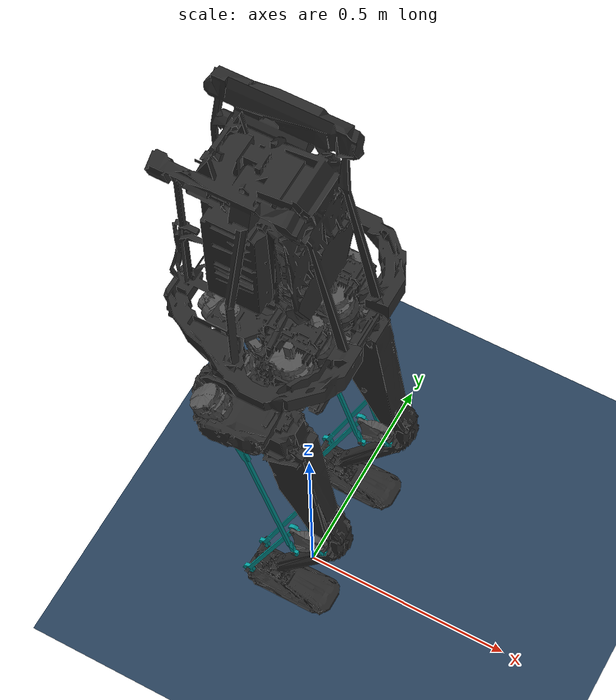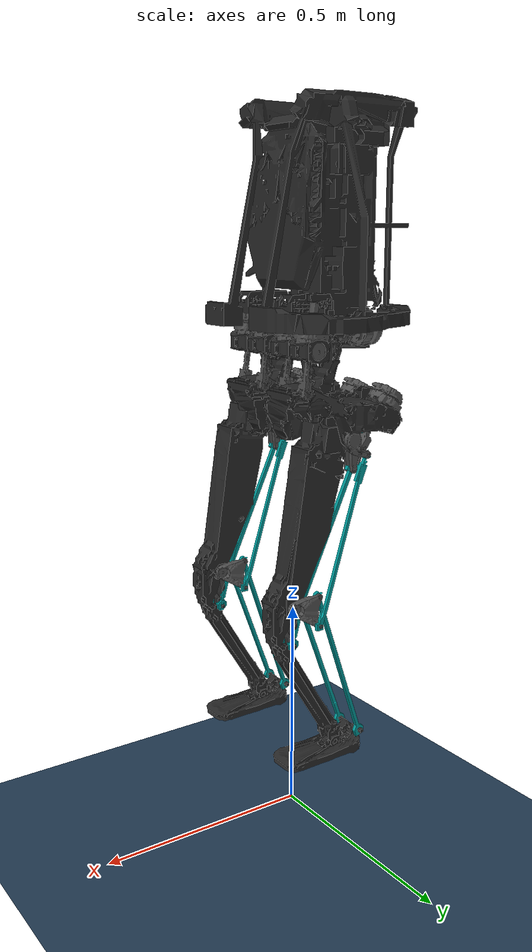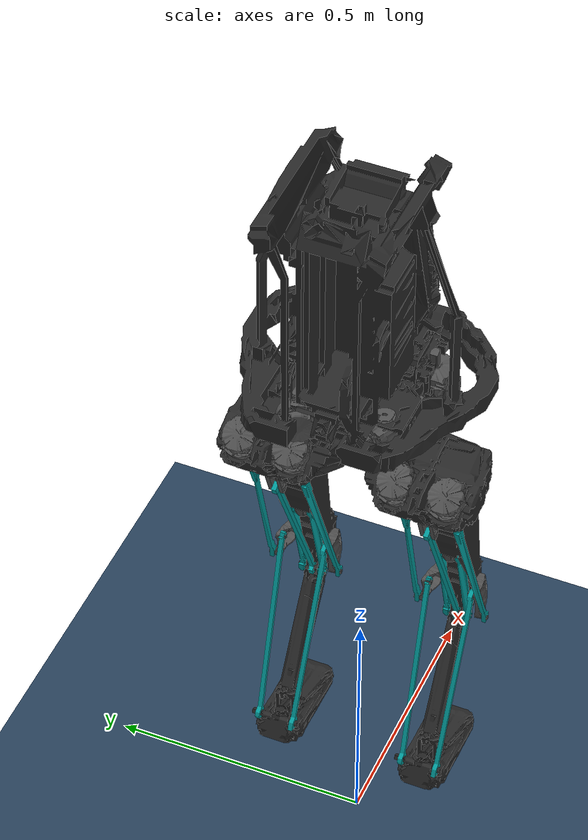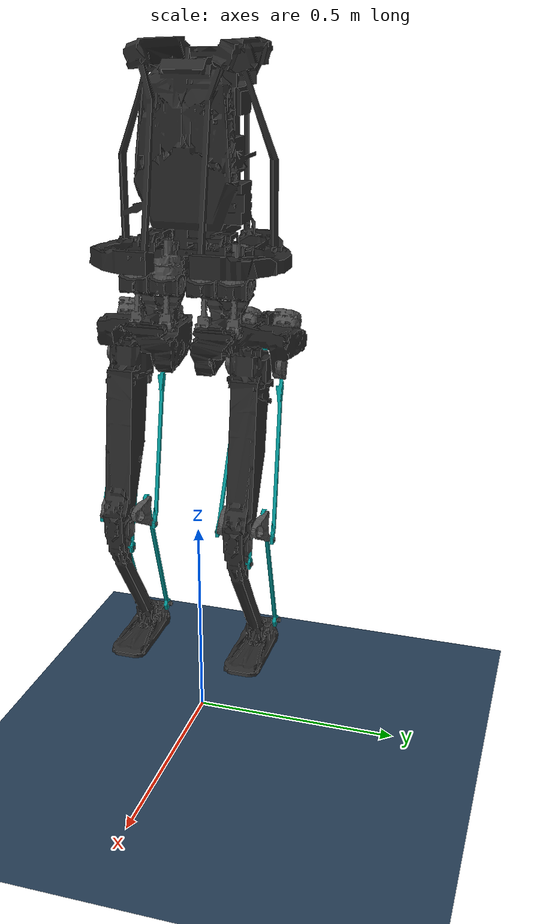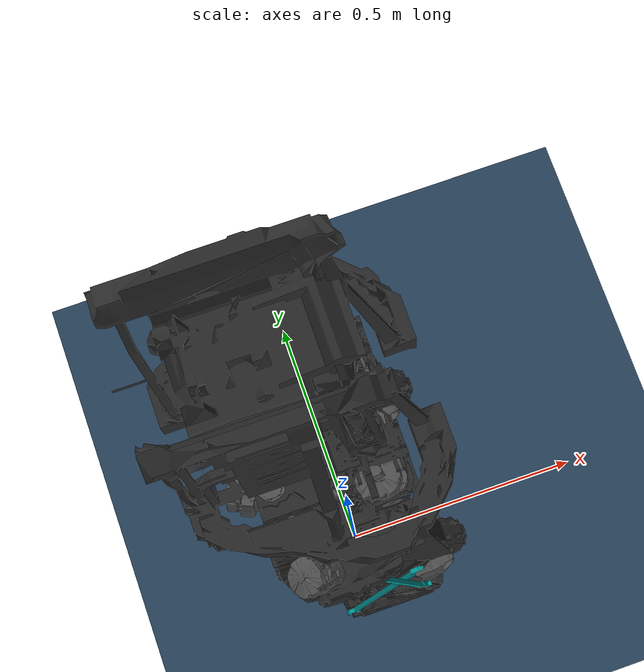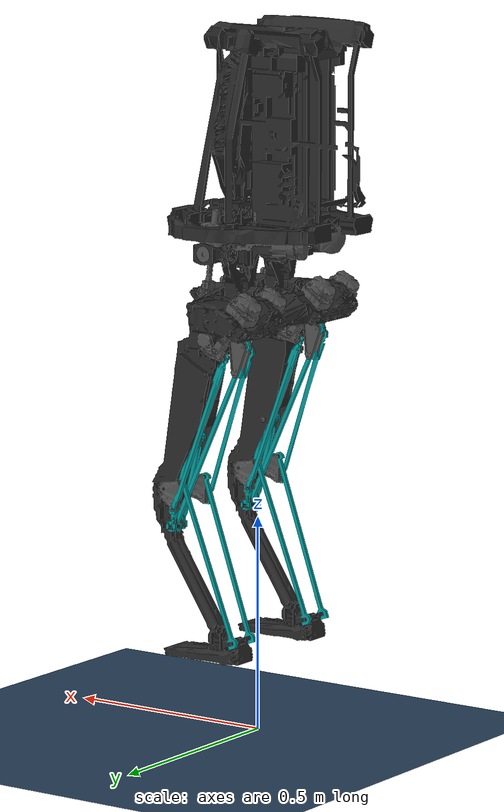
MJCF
<mujoco model="Fixed Kangaroo scene">

  <include file="kangaroo_fixed_base.xml"/>

  <visual>
    <global cameraid="-1" azimuth="160" elevation="-25" fovy="45"/>
    <headlight diffuse="0.6 0.6 0.6" ambient="0.3 0.3 0.3" specular="0 0 0"/>
    <rgba haze="0.15 0.25 0.35 1"/>
  </visual>
  <statistic center="0 0 0.8" extent="2"/>

  <asset>
        <texture type="skybox" builtin="gradient" rgb1=".3 .5 .7" rgb2="0 0 0" width="32" height="512"/>
        <texture name="body" type="cube" builtin="flat" mark="cross" width="128" height="128" rgb1="0.8 0.6 0.4" rgb2="0.8 0.6 0.4" markrgb="1 1 1" random="0.01"/>
        <material name="body" texture="body" texuniform="true" rgba="0.8 0.6 .4 1"/>
        <texture name="grid" type="2d" builtin="checker" width="512" height="512" rgb1=".1 .2 .3" rgb2=".2 .3 .4"/>
        <material name="grid" texture="grid" texrepeat="1 1" texuniform="true" reflectance=".2"/>
  </asset>

  <worldbody>
    <light name="spotlight" mode="targetbodycom" target="torso" diffuse=".8 .8 .8" specular="0.3 0.3 0.3" pos="0 -6 4" cutoff="30"/>
  	<geom name="floor" size="0 0 .05" type="plane" material="grid" condim="3"/>
  </worldbody>

</mujoco>

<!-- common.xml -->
<mujoco model="common">

<compiler angle="radian" meshdir="assets" />
    <size njmax="500" nconmax="200" />
    <option timestep="0.001" iterations="100" tolerance="1e-10" solver="Newton" integrator="Euler" jacobian="dense" cone="pyramidal" />
    <option>
        <flag multiccd="enable"/>
    </option>
    <default>
        <!--geom contype="0" conaffinity="1" size="0.1"/-->
        <joint frictionloss=".1" damping="3" limited="true" />
        <equality solref="0.005 1"/>
        <default class="collision">
      		<geom group="3" rgba="1. 0.65 0. 0.1" type="mesh"/>
    	</default>
    	<default class="box_collision">
      		<geom group="3" rgba="1. 0.65 0. 0.1" type="box" solref="0.002 1" solimp="0.9 0.95 0.001 0.05 8"/>
    	</default>
        <default class="visual">
      		<geom group="1" conaffinity="0" contype="0" type="mesh" />
    	</default>
    </default>

    <visual>
        <global offwidth="1280" offheight="1280"/>
    </visual>
</mujoco>

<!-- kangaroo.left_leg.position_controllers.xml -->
<mujoco model="kangaroo_left_leg_position_controllers">

	<actuator>
    	<position name="leg_left_1_actuator_position" 		joint="leg_left_1_motor" 		kp="300000"  timeconst="0" ctrllimited="true" ctrlrange="-0.02 0.02" forcelimited="true" forcerange="-3000 3000"/>
		<position name="leg_left_2_actuator_position" 		joint="leg_left_2_motor" 		kp="700000"  timeconst="0" ctrllimited="true" ctrlrange="-0.04 0.04" forcelimited="true" forcerange="-3000 3000"/>
		<position name="leg_left_3_actuator_position" 		joint="leg_left_3_motor" 		kp="700000"  timeconst="0" ctrllimited="true" ctrlrange="-0.04 0.04" forcelimited="true" forcerange="-3000 3000"/>
		<position name="leg_left_length_actuator_position" 	joint="leg_left_length_motor" 	kp="1000000" timeconst="0" ctrllimited="true" ctrlrange="0 0.15"	 forcelimited="true" forcerange="-5000 5000"/>
		<position name="leg_left_4_actuator_position" 		joint="leg_left_4_motor" 		kp="800000"  timeconst="0" ctrllimited="true" ctrlrange="-0.02 0.02" forcelimited="true" forcerange="-3000 3000"/>
		<position name="leg_left_5_actuator_position" 		joint="leg_left_5_motor" 		kp="800000"  timeconst="0" ctrllimited="true" ctrlrange="-0.02 0.02" forcelimited="true" forcerange="-3000 3000"/>
	</actuator>

</mujoco>

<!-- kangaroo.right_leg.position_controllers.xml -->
<mujoco model="kangaroo_right_leg_position_controllers">

	<actuator>
	    <position name="leg_right_1_actuator_position" 		joint="leg_right_1_motor" 		kp="300000"  timeconst="0" ctrllimited="true" ctrlrange="-0.02 0.02"	forcelimited="true" forcerange="-3000 3000" />
	    <position name="leg_right_2_actuator_position" 		joint="leg_right_2_motor" 		kp="700000"  timeconst="0" ctrllimited="true" ctrlrange="-0.04 0.04"	forcelimited="true" forcerange="-3000 3000" />
		<position name="leg_right_3_actuator_position" 		joint="leg_right_3_motor" 		kp="700000"  timeconst="0" ctrllimited="true" ctrlrange="-0.04 0.04"	forcelimited="true" forcerange="-3000 3000" />
		<position name="leg_right_length_actuator_position" joint="leg_right_length_motor" 	kp="1000000" timeconst="0" ctrllimited="true" ctrlrange="0 0.15"		forcelimited="true" forcerange="-5000 5000" />
		<position name="leg_right_4_actuator_position" 		joint="leg_right_4_motor" 		kp="800000"  timeconst="0" ctrllimited="true" ctrlrange="-0.02 0.02"	forcelimited="true" forcerange="-3000 3000" />
		<position name="leg_right_5_actuator_position" 		joint="leg_right_5_motor" 		kp="800000"  timeconst="0" ctrllimited="true" ctrlrange="-0.02 0.02"	forcelimited="true" forcerange="-3000 3000" />
  	</actuator>

</mujoco>

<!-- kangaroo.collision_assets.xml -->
<mujoco model="kangaroo_collision_assets">

	<mesh name="torso_collision" file="simple/Torso.STL" />
	<mesh name="base_link_collision" file="simple/base_link.STL" />
	<mesh name="Yaw_motor_collision" file="simple/Yaw_motor.STL" />
	<mesh name="Hip_yaw_collision" file="simple/Hip_yaw.STL" />
    	<mesh name="Ankle_roll_collision" file="simple/Ankle_roll.STL"/>
    	<mesh name="Knee_collision" file="simple/Knee.STL"/>
    	<mesh name="Femour_pitch_collision" file="simple/Femour_pitch.STL"/>
    	<mesh name="Hip_roll_collision" file="simple/Hip_roll.STL"/>
    	<mesh name="Hip_roll1_collision" file="simple/Hip_roll.STL" scale="-1 1 1"/>
    	<mesh name="Hip_differential_internal_cradle_collision" file="simple/Hip_differential_internal_cradle.STL" />
    	<mesh name="Hip_differential_internal_cradle2_collision" file="simple/Hip_differential_internal_cradle.STL" scale="-1 1 1"/>
    	<mesh name="Rear_triangle_collision" file="simple/Rear_triangle.STL" />
    	<mesh name="Rear_long_bar_collision" file="simple/Rear_long_bar.STL" />
    	<mesh name="External_butterfly_collision" file="simple/External_butterfly.STL" />
    	<mesh name="External_butterfly1_collision" file="simple/External_butterfly.STL" scale="1 1 -1"/>
    	<mesh name="External_higher_ankle_bar_collision" file="simple/External_higher_ankle_bar.STL" />
    	<mesh name="External_higher_ankle_bar1_collision" file="simple/External_higher_ankle_bar.STL" scale="1 1 -1"/>
    	<mesh name="External_lower_ankle_bar_collision" file="simple/External_lower_ankle_bar.STL" />

    	<mesh name="Yaw_motor1_collision" file="simple/Yaw_motor.STL" scale="1 -1 1" />
    	<mesh name="Hip_yaw1_collision" file="simple/Hip_yaw.STL" scale="1 -1 1" />
    	<mesh name="Hip_differential_internal_cradle3_collision" file="simple/Hip_differential_internal_cradle.STL" scale="-1 1 -1" />
    	<mesh name="Hip_differential_internal_cradle22_collision" file="simple/Hip_differential_internal_cradle.STL" scale="1 1 -1" />

</mujoco>

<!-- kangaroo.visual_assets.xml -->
<mujoco model="kangaroo_visual_assets">

	<mesh name="torso" file="Torso.STL" />

        <mesh name="base_link" file="base_link.STL" />
        <mesh name="Yaw_motor" file="Yaw_motor.STL" />
        <mesh name="Hip_yaw" file="Hip_yaw.STL" />
        <mesh name="Yaw_rod" file="Yaw_rod.STL"/>
        <mesh name="Hip_roll" file="Hip_roll.STL"/>
        <mesh name="Hip_pitch" file="Hip_pitch.STL"/>
        <mesh name="Hip_differential_internal_cradle" file="Hip_differential_internal_cradle.STL" />
        <mesh name="Hip_differential_internal_UnivJoint" file="Hip_differential_internal_UnivJoint.STL" />
        <mesh name="Hip_differential_internal_motor" file="Hip_differential_internal_motor.STL" scale="1 -1 1"/>
        <mesh name="Hip_differential_internal_rod" file="Hip_differential_internal_rod.STL" scale="1 1 -1"/>
        <mesh name="Hip_differential_internal_rod1" file="Hip_differential_internal_rod.STL" scale="-1 1 -1"/>

        <mesh name="Yaw_motor1" file="Yaw_motor.STL" scale="1 -1 1" />
        <mesh name="Hip_yaw1" file="Hip_yaw.STL" scale="1 -1 1" />
        <mesh name="Yaw_rod1" file="Yaw_rod.STL" scale="1 1 -1"/>
        <mesh name="Hip_roll1" file="Hip_roll.STL" scale="-1 1 1" />
        <mesh name="Hip_pitch1" file="Hip_pitch.STL" scale="-1 1 1"/>
        <mesh name="Hip_differential_internal_cradle1" file="Hip_differential_internal_cradle.STL" scale="-1 1 1" />
        <mesh name="Hip_differential_internal_UnivJoint1" file="Hip_differential_internal_UnivJoint.STL" scale="-1 1 1"/>
        <mesh name="Hip_differential_internal_cradle2" file="Hip_differential_internal_cradle.STL" scale="1 1 -1" />
        <mesh name="Hip_differential_internal_cradle3" file="Hip_differential_internal_cradle.STL" scale="-1 1 -1" />

        <mesh name="Femour_pitch" file="Femour_pitch.STL" />
        <mesh name="Knee" file="Knee.STL" />
        <mesh name="Femour_pitch1" file="Femour_pitch.STL" scale="1 1 -1" />
        <mesh name="Leg_length_slidinig_nut" file="Leg_length_slidinig_nut.STL"/>
        <mesh name="Leg_length_short_bars" file="Leg_length_short_bars.STL"/>
        <mesh name="Rear_triangle" file="Rear_triangle.STL" />
        <mesh name="Rear_long_bar" file="Rear_long_bar.STL" />
        <mesh name="Rear_short_bar" file="Rear_short_bar.STL" />

        <mesh name="External_butterfly" file="External_butterfly.STL" />
        <mesh name="External_higher_ankle_bar" file="External_higher_ankle_bar.STL" />
        <mesh name="External_lower_ankle_bar" file="External_lower_ankle_bar.STL" />
        <mesh name="External_butterfly1" file="External_butterfly.STL" scale="1 1 -1" />
        <mesh name="External_higher_ankle_bar1" file="External_higher_ankle_bar.STL" scale="1 1 -1" />
        <mesh name="External_ankle_ball" file="External_ankle_ball.STL"/>
        <mesh name="Ankle_roll" file="Ankle_roll.STL"/>
        <mesh name="Ankle_pitch" file="Ankle_pitch.STL"/>
        <mesh name="External_knee_ball" file="External_knee_ball.STL"/>
        <mesh name="Ankle_external_motor" file="Ankle_external_motor.STL"/>
        <mesh name="Ankle_external_rod" file="Ankle_external_rod.STL"/>
        <mesh name="Ankle_external_pendulum" file="Ankle_external_pendulum.STL"/>
        <mesh name="Ankle_external_pendulum1" file="Ankle_external_pendulum.STL" scale="1 1 -1"/>

</mujoco>

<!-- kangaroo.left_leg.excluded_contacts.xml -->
<mujoco model="kangaroo_left_leg_excluded_contacts">

	<exclude body1="left_yaw_motor" body2="torso" />
	<exclude body1="left_hip_yaw" body2="torso" />

	<exclude body1="base_link" body2="left_yaw_motor" />
    	<exclude body1="left_hip_roll" body2="left_hip_yaw" />
    	<exclude body1="base_link" body2="left_hip_yaw" />

    	<exclude body1="base_link" body2="left_hip_differential_3_cradle" />
    	<exclude body1="left_hip_yaw" body2="left_hip_differential_3_cradle" />

    	<exclude body1="base_link" body2="left_hip_differential_2_cradle" />
    	<exclude body1="left_hip_yaw" body2="left_hip_differential_2_cradle" />
    	<exclude body1="left_hip_differential_3_cradle" body2="left_hip_differential_2_cradle" />

    	<exclude body1="left_knee" body2="left_ankle_roll" />

    	<exclude body1="left_rear_triangle" body2="left_hip_roll" />
    	<exclude body1="left_rear_triangle" body2="left_femour_pitch" />

    	<exclude body1="left_knee" body2="left_rear_long_bar" />
    	<exclude body1="left_femour_pitch" body2="left_rear_long_bar" />

    	<exclude body1="left_5_butterfly" body2="left_femour_pitch" />
    	<exclude body1="left_5_butterfly" body2="left_knee" />
    	<exclude body1="left_5_butterfly" body2="left_5_higher_ankle_bar" />
    	<exclude body1="left_5_butterfly" body2="left_5_lower_ankle_bar" />
    	<exclude body1="left_femour_pitch" body2="left_5_lower_ankle_bar" />

    	<exclude body1="left_4_butterfly" body2="left_femour_pitch" />
    	<exclude body1="left_4_butterfly" body2="left_knee" />
    	<exclude body1="left_4_butterfly" body2="left_4_higher_ankle_bar" />
    	<exclude body1="left_4_butterfly" body2="left_4_lower_ankle_bar" />
    	<exclude body1="left_femour_pitch" body2="left_4_lower_ankle_bar" />

</mujoco>

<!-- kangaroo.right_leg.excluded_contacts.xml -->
<mujoco model="kangaroo_right_leg_excluded_contacts">

	<exclude body1="right_yaw_motor" body2="torso" />
	<exclude body1="right_hip_yaw" body2="torso" />

    	<exclude body1="base_link" body2="right_yaw_motor" />
    	<exclude body1="right_hip_roll" body2="right_hip_yaw" />
    	<exclude body1="base_link" body2="right_hip_yaw" />

    	<exclude body1="base_link" body2="right_hip_differential_3_cradle" />
    	<exclude body1="right_hip_yaw" body2="right_hip_differential_3_cradle" />

    	<exclude body1="base_link" body2="right_hip_differential_2_cradle" />
    	<exclude body1="right_hip_yaw" body2="right_hip_differential_2_cradle" />
    	<exclude body1="right_hip_differential_3_cradle" body2="right_hip_differential_2_cradle" />

    	<exclude body1="right_knee" body2="right_ankle_roll" />

    	<exclude body1="right_rear_triangle" body2="right_hip_roll" />
    	<exclude body1="right_rear_triangle" body2="right_femour_pitch" />

    	<exclude body1="right_knee" body2="right_rear_long_bar" />
    	<exclude body1="right_femour_pitch" body2="right_rear_long_bar" />

    	<exclude body1="right_5_butterfly" body2="right_femour_pitch" />
    	<exclude body1="right_5_butterfly" body2="right_knee" />
    	<exclude body1="right_5_butterfly" body2="right_5_higher_ankle_bar" />
    	<exclude body1="right_5_butterfly" body2="right_5_lower_ankle_bar" />
    	<exclude body1="right_femour_pitch" body2="right_5_lower_ankle_bar" />

    	<exclude body1="right_4_butterfly" body2="right_femour_pitch" />
    	<exclude body1="right_4_butterfly" body2="right_knee" />
    	<exclude body1="right_4_butterfly" body2="right_4_higher_ankle_bar" />
    	<exclude body1="right_4_butterfly" body2="right_4_lower_ankle_bar" />
    	<exclude body1="right_femour_pitch" body2="right_4_lower_ankle_bar" />

</mujoco>

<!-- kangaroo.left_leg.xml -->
<mujoco model="kangaroo_left_leg">
		<body name="left_yaw_motor" pos="-0.11139 0.080871 -0.0295" quat="0.838675 0 0 -0.544632">
		    <inertial pos="-4.12759e-05 -0.0164786 -0.00015095" quat="0.486534 0.507135 0.51408 0.491754" mass="0.69585" diaginertia="0.000299852 0.000207411 0.000191405" />
		    <joint name="left_yaw_motor_joint" pos="0 0 0" axis="0 0 -1"  range="-3.14159 3.14159" />
		    <geom class="visual" rgba="0.3125 0.3125 0.3125 1" mesh="Yaw_motor" />
		    <!-- geom class="collision" mesh="Yaw_motor_collision" /-->
		    <body name="left_yaw_rod" pos="0 0.0877 0" quat="-2.59734e-06 -2.59735e-06 0.707108 0.707105">
		        <inertial pos="4.22293e-05 1.30303e-05 -0.0477619" quat="1 2.01782e-05 0.000314368 1.45758e-06" mass="0.124518" diaginertia="6.62456e-05 6.33915e-05 5.54517e-06" />
		        <joint name="leg_left_1_motor" pos="0 0 0" axis="0 0 -1" type="slide"  range="-0.02 0.02" armature="0.01"/>
		        <geom class="visual" rgba="0.3125 0.3125 0.3125 1" mesh="Yaw_rod" />
		    </body>
		</body>
		<body name="left_hip_yaw" pos="-0.015 0.08 -0.0585" quat="0.707105 0 0 -0.707108">
		    <inertial pos="0.00258003 0.0184071 -0.000835982" quat="0.692006 0.0134437 -0.0540701 0.719739" mass="0.867837" diaginertia="0.00107851 0.00094694 0.000566359" />
		    <joint name="leg_left_1_joint" pos="0 0 0" axis="0 0 -1"  range="-0.785398 0.261799" />
		    <geom class="visual" rgba="0.15625 0.15625 0.15625 1" mesh="Hip_yaw" />
		    <!-- geom class="collision" mesh="Hip_yaw_collision" /-->
		    <body name="left_hip_pitch" pos="0 0.015 -0.0925" quat="0.500023 -0.499977 0.500023 -0.499977">
		    	<inertial pos="-0.00299643 6.76272e-10 0.000101293" quat="0 0.706726 0 0.707487" mass="0.0907288" diaginertia="3.90471e-05 3.64238e-05 6.10398e-06" />
		    	<joint name="leg_left_2_joint" pos="0 0 0" axis="0 0 -1"  range="-0.741743 0.741743" />
		    	<geom class="visual" rgba="0.15625 0.15625 0.15625 1" mesh="Hip_pitch" />
		    	<body name="left_hip_roll" pos="0 0 0" quat="0 0.707107 0 0.707107">
	       		<inertial pos="-0.034266 -0.039022 0.0098612" quat="0.996845 0.0323134 -0.0722423 -0.00612893" mass="2.07276" diaginertia="0.00317337 0.00292998 0.00181726" />
		        	<joint name="leg_left_3_joint" pos="0 0 0" axis="0 0 -1"  range="-0.471225 0.471225" />
		        	<geom class="visual" rgba="0.15625 0.15625 0.15625 1" mesh="Hip_roll" />
		        	<!-- geom class="collision" mesh="Hip_roll_collision" /-->
		        	<body name="left_hip_differential_3_univ" pos="0.035 0 -0.06" quat="1.34924e-11 -3.67321e-06 1 -3.67321e-06">
		    			<inertial pos="0.000576673 -0.000569156 0.000883795" quat="0.708446 0.000520642 -0.000532559 0.705765" mass="0.0543984" diaginertia="8.6648e-06 8.12417e-06 1.74562e-06" />
		    			<joint name="left_hip_differential_3_univ_joint" pos="0 0 0" axis="0 0 -1"  range="-3.14159 3.14159" />
		    			<geom class="visual" rgba="0.3125 0.3125 0.3125 1" mesh="Hip_differential_internal_UnivJoint" />
				</body>
				<body name="left_hip_differential_2_univ" pos="-0.035 0 -0.06" quat="1.34924e-11 -3.67321e-06 1 -3.67321e-06">
		    			<inertial pos="0.000576673 -0.000569156 0.000883795" quat="0.705765 0.000532559 -0.000520642 0.708446" mass="0.0543984" diaginertia="8.6648e-06 8.12417e-06 1.74562e-06" />
		    			<joint name="left_hip_differential_2_univ_joint" pos="0 0 0" axis="0 0 -1"  range="-3.14159 3.14159" />
		    			<geom class="visual" rgba="0.3125 0.3125 0.3125 1" mesh="Hip_differential_internal_UnivJoint1" />
				</body>
				<body name="left_femour_pitch" pos="-0.0669 -0.09 0" quat="0.707107 0 0.707107 0">
		    			<inertial pos="0.0581756 -0.0985134 -0.000235611" quat="0.41105 0.540325 -0.45448 0.576658" mass="2.17531" diaginertia="0.00982345 0.0096015 0.00160448" />
		    			<joint name="leg_left_femour_joint" pos="0 0 0" axis="0 0 -1"  range="-3.14159 3.14159" />
		    			<geom class="visual" rgba="0.15625 0.15625 0.15625 1" mesh="Femour_pitch" />
		    			<!-- geom class="collision" mesh="Femour_pitch_collision" /-->
		    			<body name="left_leg_length_slidinig_nut" pos="0.0686614 -0.238494 0" quat="0.537688 0.459229 0.537688 -0.459229">
		        			<inertial pos="0.000256985 0.00147139 -0.0334786" quat="0.673442 -0.0196852 0.0114763 0.738888" mass="0.5431" diaginertia="0.000173544 0.000166097 0.000112441" />
		        			<joint name="leg_left_length_motor" pos="0 0 0" axis="0 0 -1" type="slide"  range="0 0.15" armature="0.01"/>
		        			<geom class="visual" rgba="0.3125 0.3125 0.3125 1" mesh="Leg_length_slidinig_nut" />
		        			<body name="left_leg_length_short_bars" pos="0 0 0" quat="0.537687 -0.459229 -0.53769 0.459229">
		            				<inertial pos="0.0267413 -0.104163 -1.78443e-07" quat="0.433399 0.558718 -0.433399 0.558718" mass="0.240632" diaginertia="0.000242831 0.000239491 7.35858e-06" />
		            				<joint name="left_leg_length_short_bars_joint" pos="0 0 0" axis="0 0 -1"  range="-3.14159 3.14159" />
		            				<geom class="visual" rgba="0. 0.597 0.597 1" mesh="Leg_length_short_bars" />
		        			</body>
		    			</body>
				    	<body name="left_knee" pos="0.129968 -0.357083 0">
						<inertial pos="-0.0212646 -0.118028 0.000114812" quat="0.553219 0.443166 -0.551358 0.43995" mass="0.621373" diaginertia="0.00120489 0.00113669 0.000229921" />
						<joint name="leg_left_knee_joint" pos="0 0 0" axis="0 0 -1"  range="0. 3.14159" />
						<geom class="visual" rgba="0.15625 0.15625 0.15625 1" mesh="Knee" />
						<!-- geom class="collision" mesh="Knee_collision" /-->
						<body name="left_ankle_pitch" pos="-0.129989 -0.357075 0" quat="0.984808 0 0 -0.173648">
		    					<inertial pos="-0.00759995 5.88281e-08 6.94997e-09" quat="0.500003 0.499998 0.500002 0.499997" mass="0.0905838" diaginertia="2.98863e-05 2.92763e-05 4.05264e-06" />
		    					<joint name="leg_left_4_joint" pos="0 0 0" axis="0 0 1"  range="-0.741743 0.741743" />
		    					<geom class="visual" rgba="0.15625 0.15625 0.15625 1" mesh="Ankle_pitch" />
		    					<body name="left_ankle_roll" pos="0 0 0" quat="0.707105 0 0.707108 0">
		        					<inertial pos="-3.91652e-05 -0.00990525 0.022055" quat="0.698576 -0.10946 0.109446 0.698593" mass="0.413448" diaginertia="0.00138104 0.00117078 0.000258562" />
		        					<joint name="leg_left_5_joint" pos="0 0 0" axis="0 0 -1"  range="-0.471225 0.471225" />
		        					<geom class="visual" rgba="0.15625 0.15625 0.15625 1" mesh="Ankle_roll" />
		        					<geom class="box_collision" size="0.045 0.0125 0.105" pos="0 -0.005 0.04" quat="0.984808 -0.173648 0. 0." name="left_ankle_roll"/>
		    					</body>
						</body>
						<body name="left_5_butterfly" pos="0 0 -0.043">
		    					<inertial pos="-0.0248716 -0.00598892 -0.00506167" quat="0.489871 0.39472 -0.65931 0.411742" mass="0.082315" diaginertia="4.23395e-05 2.49809e-05 2.09854e-05" />
		    					<joint name="left_5_butterfly_joint" pos="0 0 0" axis="0 0 -1"  range="-3.14159 3.14159" />
		    					<geom class="visual" rgba="0.3125 0.3125 0.3125 1" mesh="External_butterfly" />
		    					<!-- geom class="collision" mesh="External_butterfly_collision" /-->
		    					<body name="left_5_knee_ball" pos="-0.056381 0.020521 0.0005" quat="1.34924e-11 3.67321e-06 -1 -3.67321e-06">
		        					<inertial pos="3.40809e-12 -8.79985e-12 0" quat="0.5 0.5 -0.5 0.5" mass="0.00195231" diaginertia="4.30053e-08 3.17847e-08 3.17847e-08" />
		        					<joint name="left_5_knee_ball_joint" pos="0 0 0" axis="0 0 -1"  range="-3.14159 3.14159" />
		        					<body name="left_5_lower_ankle_bar" pos="0 0 0" quat="0.696359 -0.12281 0.696362 0.12281">
		            						<inertial pos="0.00431894 -0.218831 -6.75122e-08" quat="0.707072 0.707072 0.00697723 0.00697723" mass="0.125467" diaginertia="0.000608718 0.000607712 2.48422e-06" />
		            						<joint name="left_5_lower_ankle_bar_joint" pos="0 0 0" axis="0 0 -1"  range="-3.14159 3.14159" />
		            						<geom class="visual" rgba="0 0.597656 0.597656 1" mesh="External_lower_ankle_bar" />
		            						<!-- geom class="collision" mesh="External_lower_ankle_bar_collision" /-->
		        					</body>
		    					</body>
						</body>
						<body name="left_4_butterfly" pos="0 0 0.043">
		    					<inertial pos="-0.0248716 -0.00598892 0.00506167" quat="0.65931 0.411742 -0.489871 0.39472" mass="0.082315" diaginertia="4.23395e-05 2.49809e-05 2.09854e-05" />
		    					<joint name="left_4_butterfly_joint" pos="0 0 0" axis="0 0 -1"  range="-3.14159 3.14159" />
		    					<geom class="visual" rgba="0.3125 0.3125 0.3125 1" mesh="External_butterfly1" />
		    					<!-- geom class="collision" mesh="External_butterfly1_collision" /-->
		    					<body name="left_4_knee_ball" pos="-0.056381 0.020521 -0.0005" quat="1.34924e-11 3.67321e-06 -1 -3.67321e-06">
		        					<inertial pos="3.40809e-12 -8.79985e-12 0" quat="0.5 0.5 -0.5 0.5" mass="0.00195231" diaginertia="4.30053e-08 3.17847e-08 3.17847e-08" />
		        					<joint name="left_4_knee_ball_joint" pos="0 0 0" axis="0 0 -1"  range="-3.14159 3.14159" />
		        					<geom class="visual" rgba="0.15625 0.15625 0.15625 1" mesh="External_knee_ball" />
		        					<body name="left_4_lower_ankle_bar" pos="0 0 0" quat="0.696359 0.12281 -0.696362 0.12281">
		            						<inertial pos="0.00431894 -0.218831 -6.75122e-08" quat="0.707072 0.707072 0.00697723 0.00697723" mass="0.125467" diaginertia="0.000608718 0.000607712 2.48422e-06" />
		            						<joint name="left_4_lower_ankle_bar_joint" pos="0 0 0" axis="0 0 -1"  range="-3.14159 3.14159" />
		            						<geom class="visual" rgba="0 0.597656 0.597656 1" mesh="External_lower_ankle_bar" />
		            						<!-- geom class="collision" mesh="External_lower_ankle_bar_collision" /-->
		        					</body>
		    					</body>
						</body>
				    	</body>
				</body>
				<body name="left_ankle_5_motor" pos="-0.115 -0.04665 0.0750844" quat="0.707107 0 -0.707107 0">
		    					<inertial pos="0.00976486 0.0132739 -0.00015095" quat="0.641742 0.615224 0.316284 0.331106" mass="0.69585" diaginertia="0.000299852 0.000207411 0.000191405" />
		    					<joint name="left_ankle_5_motor_joint" pos="0 0 0" axis="0 0 1"  range="-3.14159 3.14159" />
		    					<geom class="visual" rgba="0.3125 0.3125 0.3125 1" mesh="Ankle_external_motor" />
		    					<body name="left_ankle_5_rod" pos="-0.0464141 -0.0634252 0" quat="0.630586 0.319939 -0.630586 0.319939">
		        					<inertial pos="-1.30338e-05 4.22282e-05 -0.0477619" quat="0.707105 -0.000208025 0.000236665 0.707109" mass="0.124518" diaginertia="6.62458e-05 6.33917e-05 5.54517e-06" />
		        					<joint name="leg_left_5_motor" pos="0 0 0" axis="0 0 -1" type="slide"  range="-0.02 0.02" armature="0.01"/>
		        					<geom class="visual" rgba="0.3125 0.3125 0.3125 1" mesh="Ankle_external_rod" />
		    					</body>
				</body>
				<body name="left_ankle_5_pendulum" pos="-0.115 -0.09 0" quat="0.707107 0 -0.707107 0">
		    			<inertial pos="0.015271 -0.0163076 0.00749039" quat="0.179908 0.712185 -0.255833 0.62847" mass="0.0647795" diaginertia="2.48188e-05 2.14378e-05 7.19264e-06" />
		    			<joint name="left_ankle_5_pendulum_joint" pos="0 0 0" axis="0 0 -1"  range="-3.14159 3.14159" />
		    			<geom class="visual" rgba="0.3125 0.3125 0.3125 1" mesh="Ankle_external_pendulum" />
		    			<body name="left_5_higher_ankle_bar" pos="0.0459627 -0.0385673 0" quat="0 0 -1 0">
		        			<inertial pos="0.0635711 -0.17466 -0.00880435" quat="0.395868 0.592773 -0.415064 0.565359" mass="0.108309" diaginertia="0.000634318 0.000633977 1.61866e-06" />
		        			<joint name="left_5_higher_ankle_bar_joint" pos="0 0 0" axis="0 0 -1"  range="-3.14159 3.14159" />
		        			<geom class="visual" rgba="0 0.597656 0.597656 1" mesh="External_higher_ankle_bar" />
		        			<!-- geom class="collision" mesh="External_higher_ankle_bar_collision" /-->
		    			</body>
				</body>
				<body name="left_ankle_4_motor" pos="-0.019 -0.04665 0.0750844" quat="0.707107 0 -0.707107 0">
		    			<inertial pos="0.00976486 0.0132739 -0.00015095" quat="0.641742 0.615224 0.316284 0.331106" mass="0.69585" diaginertia="0.000299852 0.000207411 0.000191405" />
		    			<joint name="left_ankle_4_motor_joint" pos="0 0 0" axis="0 0 1"  range="-3.14159 3.14159" />
		    			<geom class="visual" rgba="0.3125 0.3125 0.3125 1" mesh="Ankle_external_motor" />
		    			<body name="left_ankle_4_rod" pos="-0.0464141 -0.0634252 0" quat="0.630586 0.319939 -0.630586 0.319939">
		        			<inertial pos="-1.30338e-05 4.22282e-05 -0.0477619" quat="0.707105 -0.000208025 0.000236665 0.707109" mass="0.124518" diaginertia="6.62458e-05 6.33917e-05 5.54517e-06" />
		        			<joint name="leg_left_4_motor" pos="0 0 0" axis="0 0 -1" type="slide"  range="-0.02 0.02" armature="0.01"/>
		        			<geom class="visual" rgba="0.3125 0.3125 0.3125 1" mesh="Ankle_external_rod" />
		    			</body>
				</body>
				<body name="left_ankle_4_pendulum" pos="-0.019 -0.09 0" quat="0.707107 0 -0.707107 0">
		    			<inertial pos="0.015271 -0.0163076 -0.00749039" quat="0.255833 0.62847 -0.179908 0.712185" mass="0.0647795" diaginertia="2.48188e-05 2.14378e-05 7.19264e-06" />
		    			<joint name="left_ankle_4_pendulum_joint" pos="0 0 0" axis="0 0 -1"  range="-3.14159 3.14159" />
		    			<geom class="visual" rgba="0.3125 0.3125 0.3125 1" mesh="Ankle_external_pendulum1" />
		    			<body name="left_4_higher_ankle_bar" pos="0.0459627 -0.0385673 0" quat="0 0 -1 0">
		        			<inertial pos="0.0635711 -0.17466 0.00880435" quat="0.415064 0.565359 -0.395868 0.592773" mass="0.108309" diaginertia="0.000634318 0.000633977 1.61866e-06" />
		        			<joint name="left_4_higher_ankle_bar_joint" pos="0 0 0" axis="0 0 -1"  range="-3.14159 3.14159" />
		        			<geom class="visual" rgba="0 0.597656 0.597656 1" mesh="External_higher_ankle_bar1" />
		        			<!-- geom class="collision" mesh="External_higher_ankle_bar1_collision" /-->
		    			</body>
				</body>
				<body name="left_rear_short_bar" pos="-0.0669 -0.017628 0.089372" quat="0.702633 0.0794157 0.702633 0.0794157">
		    			<inertial pos="1.87854e-07 -0.0450209 -2.80023e-07" quat="0.500004 0.500003 -0.499997 0.499996" mass="0.0877852" diaginertia="1.65445e-05 1.48746e-05 2.86491e-06" />
		    			<joint name="left_rear_short_bar_joint" pos="0 0 0" axis="0 0 -1"  range="-3.14159 3.14159" />
		    			<geom class="visual" rgba="0 0.597656 0.597656 1" mesh="Rear_short_bar" />
		    			<body name="left_rear_triangle" pos="0 -0.09 0">
		        			<inertial pos="0.0142194 -0.0194738 0.000244328" quat="0.547674 0.44333 -0.551845 0.44607" mass="0.107984" diaginertia="6.55651e-05 5.74616e-05 1.29395e-05" />
		        			<joint name="left_rear_triangle_joint" pos="0 0 0" axis="0 0 1"  range="-3.14159 3.14159" />
		        			<geom class="visual" rgba="0.3125 0.3125 0.3125 1" mesh="Rear_triangle" />
		        			<!-- geom class="collision" mesh="Rear_triangle_collision" /-->
		        	 		<body name="left_rear_long_bar" pos="0.0079432 -0.067422 0" quat="0.994748 0 0 0.102355">
		            				<inertial pos="8.99743e-08 -0.202192 -1.24412e-07" quat="0.5 0.5 -0.5 0.5" mass="0.16896" diaginertia="0.000992611 0.000990941 4.89361e-06" />
		            				<joint name="left_rear_long_bar_joint" pos="0 0 0" axis="0 0 -1"  range="-3.14159 3.14159" />
		            				<geom class="visual" rgba="0 0.597656 0.597656 1" mesh="Rear_long_bar" />
		            				<!-- geom class="collision" mesh="Rear_long_bar_collision" /-->
		        			</body>
		    			</body>
				</body>
		    	</body>
		    </body>
		    <body name="left_hip_differential_3_cradle" pos="0.035 0.0625 0.00015" quat="-2.59734e-06 -2.59735e-06 0.707108 0.707105">
		    	<inertial pos="-0.00138216 2.16955e-06 -0.0105801" quat="0.995555 -1.18897e-05 -0.0941793 7.06526e-05" mass="0.138052" diaginertia="0.000122729 0.000118601 2.99324e-05" />
		    	<joint name="left_hip_differential_3_cradle_joint" pos="0 0 0" axis="0 0 -1"  range="-3.14159 3.14159" />
		    	<geom class="visual" rgba="0.15625 0.15625 0.15625 1" mesh="Hip_differential_internal_cradle" />
		    	<!-- geom class="collision" mesh="Hip_differential_internal_cradle_collision" /-->
		    	<body name="left_hip_differential_3_motor" pos="0 0 0" quat="-2.59734e-06 0.707105 2.59735e-06 0.707108">
		        	<inertial pos="-0.0022018 0.0166124 -0.000153374" quat="0.472136 0.451722 0.522963 0.547307" mass="0.698684" diaginertia="0.000300396 0.000209312 0.00019332" />
		        	<joint name="left_hip_differential_3_motor_joint" pos="0 0 0" axis="0 0 -1"  range="-3.14159 3.14159" />
		        	<geom class="visual" rgba="0.3125 0.3125 0.3125 1" mesh="Hip_differential_internal_motor" />
		        	<body name="left_hip_differential_3_rod" pos="0.0125 0.09265 0" quat="0.465375 -0.532376 -0.465376 -0.532378">
		            		<inertial pos="0.000689102 5.28001e-05 -0.0626747" quat="0.706863 6.97452e-05 -0.000303377 0.707351" mass="0.142095" diaginertia="0.000137789 0.000136589 4.89956e-06" />
		            		<joint name="leg_left_3_motor" pos="0 0 0" axis="0 0 -1" type="slide"  range="-0.04 0.04" armature="0.01"/>
		            		<geom class="visual" rgba="0.3125 0.3125 0.3125 1" mesh="Hip_differential_internal_rod1" />
		        	</body>
		    	</body>
		    </body>
		    <body name="left_hip_differential_2_cradle" pos="-0.035 0.0625 0.00015" quat="-2.59734e-06 -2.59735e-06 0.707108 0.707105">
		    	<inertial pos="-0.00138216 2.16955e-06 -0.0105801" quat="0.995555 1.18897e-05 0.0941793 7.06526e-05" mass="0.138052" diaginertia="0.000122729 0.000118601 2.99324e-05" />
		    	<joint name="left_hip_differential_2_cradle_joint" pos="0 0 0" axis="0 0 -1"  range="-3.14159 3.14159" />
		    	<geom class="visual" rgba="0.15625 0.15625 0.15625 1" mesh="Hip_differential_internal_cradle1" />
		    	<!-- geom class="collision" mesh="Hip_differential_internal_cradle2_collision" /-->
	    		<body name="left_hip_differential_2_motor" pos="0 0 0" quat="-2.59734e-06 0.707105 2.59735e-06 0.707108">
        			<inertial pos="-0.0022018 0.0166124 -0.000153374" quat="0.472136 0.451722 0.522963 0.547307" mass="0.698684" diaginertia="0.000300396 0.000209312 0.00019332" />
		        	<joint name="left_hip_differential_2_motor_joint" pos="0 0 0" axis="0 0 -1"  range="-3.14159 3.14159" />
		        	<geom class="visual" rgba="0.3125 0.3125 0.3125 1" mesh="Hip_differential_internal_motor" />
		        	<body name="left_hip_differential_2_rod" pos="0.0125 0.09265 0" quat="0.465375 -0.532376 -0.465376 -0.532378">
		            		<inertial pos="0.000689102 5.28001e-05 -0.0626747" quat="0.706863 6.97452e-05 -0.000303377 0.707351" mass="0.142095" diaginertia="0.000137789 0.000136589 4.89956e-06" />
		            		<joint name="leg_left_2_motor" pos="0 0 0" axis="0 0 -1" type="slide"  range="-0.04 0.04" armature="0.01"/>
		            		<geom class="visual" rgba="0.3125 0.3125 0.3125 1" mesh="Hip_differential_internal_rod" />
	        		</body>
		    	</body>
		</body>
		</body>
</mujoco>

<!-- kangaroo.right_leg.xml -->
<mujoco model="kangaroo_right_leg">

<body name="right_yaw_motor" pos="-0.11139 -0.080871 -0.0295" quat="0.838675 0 0 0.544632">
		    <inertial pos="-4.12759e-05 0.0164786 -0.00015095" quat="0.491754 0.51408 0.507135 0.486534" mass="0.69585" diaginertia="0.000299852 0.000207411 0.000191405" />
		    <joint name="right_yaw_motor_joint" pos="0 0 0" axis="0 0 -1"  range="-3.14159 3.14159" />
		    <geom class="visual" rgba="0.3125 0.3125 0.3125 1" mesh="Yaw_motor1" />
		    <!-- geom class="collision" mesh="Yaw_motor1_collision" /-->
		    <body name="right_yaw_rod" pos="0 -0.0877 0" quat="-2.59734e-06 -2.59735e-06 0.707108 0.707105">
		        <inertial pos="4.22293e-05 1.30303e-05 0.0477619" quat="1 -2.01782e-05 0.000314368 -1.45758e-06" mass="0.124518" diaginertia="6.62456e-05 6.33915e-05 5.54517e-06" />
		        <joint name="leg_right_1_motor" pos="0 0 0" axis="0 0 1" type="slide"  range="-0.02 0.02" armature="0.01"/>
		        <geom class="visual" rgba="0.3125 0.3125 0.3125 1" mesh="Yaw_rod1" />
		    </body>
		</body>
		<body name="right_hip_yaw" pos="-0.015 -0.08 -0.0585" quat="0.707105 0 0 0.707108">
		    <inertial pos="0.00258003 -0.0184071 -0.000835982" quat="0.719739 -0.0540701 0.0134437 0.692006" mass="0.867837" diaginertia="0.00107851 0.00094694 0.000566359" />
		    <joint name="leg_right_1_joint" pos="0 0 0" axis="0 0 -1"  range="-0.261799 0.785398" />
		    <geom class="visual" rgba="0.15625 0.15625 0.15625 1" mesh="Hip_yaw1" />
		    <!-- geom class="collision" mesh="Hip_yaw1_collision" /-->
		    <body name="right_hip_pitch" pos="0 -0.015 -0.0925" quat="-0.499977 0.500023 0.499977 -0.500023">
		    	<inertial pos="-0.00299643 -6.76272e-10 0.000101293" quat="0 0.706726 0 0.707487" mass="0.0907288" diaginertia="3.90471e-05 3.64238e-05 6.10398e-06" />
		    	<joint name="leg_right_2_joint" pos="0 0 0" axis="0 0 -1"  range="-0.741743 0.741743" />
		    	<geom class="visual" rgba="0.15625 0.15625 0.15625 1" mesh="Hip_pitch1" />
	    		<body name="right_hip_roll" pos="0 0 0" quat="0 0.707107 0 0.707107">
		       	<inertial pos="0.034266 -0.039022 0.0098612" quat="0.996845 0.0323134 0.0722423 0.00612893" mass="2.07276" diaginertia="0.00317337 0.00292998 0.00181726" />
		        	<joint name="leg_right_3_joint" pos="0 0 0" axis="0 0 -1"  range="-0.471225 0.471225" />
		        	<geom class="visual" rgba="0.15625 0.15625 0.15625 1" mesh="Hip_roll1" />
		        	<!-- geom class="collision" mesh="Hip_roll1_collision" /-->
		        	<body name="right_hip_differential_2_univ" pos="-0.035 0 -0.06" quat="1.34924e-11 -3.67321e-06 1 -3.67321e-06">
		   		 	<inertial pos="-0.000576673 -0.000569156 0.000883795" quat="0.705765 0.000532559 -0.000520642 0.708446" mass="0.0543984" diaginertia="8.6648e-06 8.12417e-06 1.74562e-06" />
		    		 	<joint name="right_hip_differential_2_univ_joint" pos="0 0 0" axis="0 0 -1"  range="-3.14159 3.14159" />
		    		 	<geom class="visual" rgba="0.3125 0.3125 0.3125 1" mesh="Hip_differential_internal_UnivJoint1" />
				</body>
				<body name="right_hip_differential_3_univ" pos="0.035 0 -0.06" quat="1.34924e-11 -3.67321e-06 1 -3.67321e-06">
		    		 	<inertial pos="-0.000576673 -0.000569156 0.000883795" quat="0.708446 0.000520642 -0.000532559 0.705765" mass="0.0543984" diaginertia="8.6648e-06 8.12417e-06 1.74562e-06" />
		    			<joint name="right_hip_differential_3_univ_joint" pos="0 0 0" axis="0 0 -1"  range="-3.14159 3.14159" />
		    			<geom class="visual" rgba="0.3125 0.3125 0.3125 1" mesh="Hip_differential_internal_UnivJoint" />
				</body>
				<body name="right_femour_pitch" pos="0.0669 -0.09 0" quat="0.707107 0 0.707107 0">
		    			<inertial pos="0.0581756 -0.0985134 0.000235611" quat="0.45448 0.576658 -0.41105 0.540325" mass="2.17531" diaginertia="0.00982345 0.0096015 0.00160448" />
		    			<joint name="leg_right_femour_joint" pos="0 0 0" axis="0 0 -1"  range="-3.14159 3.14159" />
		    			<geom class="visual" rgba="0.15625 0.15625 0.15625 1" mesh="Femour_pitch1" />
		    			<!-- geom class="collision" mesh="Femour_pitch_collision" /-->
		    			<body name="right_leg_length_slidinig_nut" pos="0.0686614 -0.238494 0" quat="0.537688 0.459229 0.537688 -0.459229">
		        			<inertial pos="-0.000256985 0.00147139 -0.0334786" quat="0.738888 -0.0114763 0.0196852 0.673442" mass="0.5431" diaginertia="0.000173544 0.000166097 0.000112441" />
		        			<joint name="leg_right_length_motor" pos="0 0 0" axis="0 0 -1" type="slide"  range="0 0.15" armature="0.01"/>
		        			<geom class="visual" rgba="0.3125 0.3125 0.3125 1" mesh="Leg_length_slidinig_nut" />
		        			<body name="right_leg_length_short_bars" pos="0 0 0" quat="0.537687 -0.459229 -0.53769 0.459229">
		            				<inertial pos="0.0267413 -0.104163 -1.78443e-07" quat="0.433399 0.558718 -0.433399 0.558718" mass="0.240632" diaginertia="0.000242831 0.000239491 7.35858e-06" />
		            				<joint name="right_leg_length_short_bars_joint" pos="0 0 0" axis="0 0 -1"  range="-3.14159 3.14159" />
		            				<geom class="visual" rgba="0. 0.597 0.597 1" mesh="Leg_length_short_bars" />
		        			</body>
		    			</body>
		    			<body name="right_knee" pos="0.129968 -0.357083 0">
		        			<inertial pos="-0.0212646 -0.118028 -0.000114812" quat="0.551358 0.43995 -0.553219 0.443166" mass="0.621373" diaginertia="0.00120489 0.00113669 0.000229921" />
		        			<joint name="leg_right_knee_joint" pos="0 0 0" axis="0 0 -1"  range="0. 3.14159" />
		        			<geom class="visual" rgba="0.15625 0.15625 0.15625 1" mesh="Knee" />
		        			<!-- geom class="collision" mesh="Knee_collision" /-->
		        			<body name="right_ankle_pitch" pos="-0.129989 -0.357075 0" quat="0.984808 0 0 -0.173648">
		    					<inertial pos="-0.00759995 5.88281e-08 6.94997e-09" quat="0.500003 0.499998 0.500002 0.499997" mass="0.0905838" diaginertia="2.98863e-05 2.92763e-05 4.05264e-06" />
		    					<joint name="leg_right_4_joint" pos="0 0 0" axis="0 0 1"  range="-0.741743 0.741743" />
		    					<geom class="visual" rgba="0.15625 0.15625 0.15625 1" mesh="Ankle_pitch"/>
		    					<body name="right_ankle_roll" pos="0 0 0" quat="0.707105 0 0.707108 0">
		        					<inertial pos="-3.91652e-05 -0.00990525 0.022055" quat="0.698576 -0.10946 0.109446 0.698593" mass="0.413448" diaginertia="0.00138104 0.00117078 0.000258562" />
		        					<joint name="leg_right_5_joint" pos="0 0 0" axis="0 0 -1"  range="-0.471225 0.471225" />
		        					<geom class="visual" rgba="0.15625 0.15625 0.15625 1" mesh="Ankle_roll" />
		        					<geom class="box_collision" size="0.045 0.0125 0.105" pos="0 -0.005 0.04" quat="0.984808 -0.173648 0. 0." name="right_ankle_roll"/>
		    					</body>
						</body>
						<body name="right_4_butterfly" pos="0 0 0.043">
		    					<inertial pos="-0.0248716 -0.00598892 0.00506167" quat="0.65931 0.411742 -0.489871 0.39472" mass="0.082315" diaginertia="4.23395e-05 2.49809e-05 2.09854e-05" />
		    					<joint name="right_4_butterfly_joint" pos="0 0 0" axis="0 0 -1"  range="-3.14159 3.14159" />
		    					<geom class="visual" rgba="0.3125 0.3125 0.3125 1" mesh="External_butterfly1" />
		    					<!-- geom class="collision" mesh="External_butterfly1_collision" /-->
		    					<body name="right_4_knee_ball" pos="-0.056381 0.020521 -0.0005" quat="1.34924e-11 3.67321e-06 -1 -3.67321e-06">
		        					<inertial pos="3.40809e-12 -8.79985e-12 0" quat="0.5 0.5 -0.5 0.5" mass="0.00195231" diaginertia="4.30053e-08 3.17847e-08 3.17847e-08" />
								<joint name="right_4_knee_ball_joint" pos="0 0 0" axis="0 0 -1"  range="-3.14159 3.14159" />
								<geom class="visual" rgba="0.15625 0.15625 0.15625 1" mesh="External_knee_ball" />
								<body name="right_4_lower_ankle_bar" pos="0 0 0" quat="0.696359 0.12281 -0.696362 0.12281">
		    							<inertial pos="0.00431894 -0.218831 -6.75122e-08" quat="0.707072 0.707072 0.00697723 0.00697723" mass="0.125467" diaginertia="0.000608718 0.000607712 2.48422e-06" />
		    							<joint name="right_4_lower_ankle_bar_joint" pos="0 0 0" axis="0 0 -1"  range="-3.14159 3.14159" />
		    							<geom class="visual" rgba="0 0.597656 0.597656 1" mesh="External_lower_ankle_bar" />
		    							<!-- geom class="collision" mesh="External_lower_ankle_bar_collision" /-->
								</body>
		    					</body>
						</body>
						<body name="right_5_butterfly" pos="0 0 -0.043">
		    					<inertial pos="-0.0248716 -0.00598892 -0.00506167" quat="0.489871 0.39472 -0.65931 0.411742" mass="0.082315" diaginertia="4.23395e-05 2.49809e-05 2.09854e-05" />
		    					<joint name="right_5_butterfly_joint" pos="0 0 0" axis="0 0 -1"  range="-3.14159 3.14159" />
		    					<geom class="visual" rgba="0.3125 0.3125 0.3125 1" mesh="External_butterfly" />
		    					<!-- geom class="collision" mesh="External_butterfly_collision" /-->
	    						<body name="right_5_knee_ball" pos="-0.056381 0.020521 0.0005" quat="1.34924e-11 3.67321e-06 -1 -3.67321e-06">
								<inertial pos="3.40809e-12 -8.79985e-12 0" quat="0.5 0.5 -0.5 0.5" mass="0.00195231" diaginertia="4.30053e-08 3.17847e-08 3.17847e-08" />
								<joint name="right_5_knee_ball_joint" pos="0 0 0" axis="0 0 -1"  range="-3.14159 3.14159" />
								<geom class="visual" rgba="0.15625 0.15625 0.15625 1" mesh="External_knee_ball" />
								<body name="right_5_lower_ankle_bar" pos="0 0 0" quat="0.696359 -0.12281 0.696362 0.12281">
		    							<inertial pos="0.00431894 -0.218831 -6.75122e-08" quat="0.707072 0.707072 0.00697723 0.00697723" mass="0.125467" diaginertia="0.000608718 0.000607712 2.48422e-06" />
		    							<joint name="right_5_lower_ankle_bar_joint" pos="0 0 0" axis="0 0 -1"  range="-3.14159 3.14159" />
		    							<geom class="visual" rgba="0 0.597656 0.597656 1" mesh="External_lower_ankle_bar" />
		    							<!-- geom class="collision" mesh="External_lower_ankle_bar_collision" /-->
		        					</body>
		    					</body>
						</body>
		    			</body>
				</body>
				<body name="right_ankle_4_motor" pos="0.115 -0.04665 0.0750844" quat="0.707107 0 -0.707107 0">
		    			<inertial pos="0.00976486 0.0132739 -0.00015095" quat="0.641742 0.615224 0.316284 0.331106" mass="0.69585" diaginertia="0.000299852 0.000207411 0.000191405" />
		    			<joint name="right_ankle_4_motor_joint" pos="0 0 0" axis="0 0 1"  range="-3.14159 3.14159" />
		    			<geom class="visual" rgba="0.3125 0.3125 0.3125 1" mesh="Ankle_external_motor" />
		    			<body name="right_ankle_4_rod" pos="-0.0464141 -0.0634252 0" quat="0.630586 0.319939 -0.630586 0.319939">
		        			<inertial pos="-1.30338e-05 4.22282e-05 -0.0477619" quat="0.707105 -0.000208025 0.000236665 0.707109" mass="0.124518" diaginertia="6.62458e-05 6.33917e-05 5.54517e-06" />
		        			<joint name="leg_right_4_motor" pos="0 0 0" axis="0 0 -1" type="slide"  range="-0.02 0.02" armature="0.01"/>
		        			<geom class="visual" rgba="0.3125 0.3125 0.3125 1" mesh="Ankle_external_rod" />
		    			</body>
				</body>
				<body name="right_ankle_4_pendulum" pos="0.115 -0.09 0" quat="0.707107 0 -0.707107 0">
		    			<inertial pos="0.015271 -0.0163076 -0.00749039" quat="0.255833 0.62847 -0.179908 0.712185" mass="0.0647795" diaginertia="2.48188e-05 2.14378e-05 7.19264e-06" />
		    			<joint name="right_ankle_4_pendulum_joint" pos="0 0 0" axis="0 0 -1"  range="-3.14159 3.14159" />
		    			<geom class="visual" rgba="0.3125 0.3125 0.3125 1" mesh="Ankle_external_pendulum1" />
		    			<body name="right_4_higher_ankle_bar" pos="0.0459627 -0.0385673 0" quat="0 0 -1 0">
		        			<inertial pos="0.0635711 -0.17466 0.00880435" quat="0.415064 0.565359 -0.395868 0.592773" mass="0.108309" diaginertia="0.000634318 0.000633977 1.61866e-06" />
		        			<joint name="right_4_higher_ankle_bar_joint" pos="0 0 0" axis="0 0 -1"  range="-3.14159 3.14159" />
		        			<geom class="visual" rgba="0 0.597656 0.597656 1" mesh="External_higher_ankle_bar1" />
		        			<!-- geom class="collision" mesh="External_higher_ankle_bar1_collision" /-->
		    			</body>
				</body>
				<body name="right_rear_short_bar" pos="0.0669 -0.017628 0.089372" quat="0.702633 0.0794157 0.702633 0.0794157">
		    				<inertial pos="1.87854e-07 -0.0450209 -2.80023e-07" quat="0.500004 0.500003 -0.499997 0.499996" mass="0.0877852" diaginertia="1.65445e-05 1.48746e-05 2.86491e-06" />
		    				<joint name="right_rear_short_bar_joint" pos="0 0 0" axis="0 0 -1"  range="-3.14159 3.14159" />
		    				<geom class="visual" rgba="0 0.597656 0.597656 1" mesh="Rear_short_bar" />
		    				<body name="right_rear_triangle" pos="0 -0.09 0">
		        				<inertial pos="0.0142194 -0.0194738 0.000244328" quat="0.547674 0.44333 -0.551845 0.44607" mass="0.107984" diaginertia="6.55651e-05 5.74616e-05 1.29395e-05" />
		        				<joint name="right_rear_triangle_joint" pos="0 0 0" axis="0 0 1"  range="-3.14159 3.14159" />
		        				<geom class="visual" rgba="0.3125 0.3125 0.3125 1" mesh="Rear_triangle" />
		        				<!-- geom class="collision" mesh="Rear_triangle_collision" /-->
		        				<body name="right_rear_long_bar" pos="0.0079432 -0.067422 0" quat="0.994748 0 0 0.102355">
		           	 				<inertial pos="8.99743e-08 -0.202192 -1.24412e-07" quat="0.5 0.5 -0.5 0.5" mass="0.16896" diaginertia="0.000992611 0.000990941 4.89361e-06" />
		            					<joint name="right_rear_long_bar_joint" pos="0 0 0" axis="0 0 -1"  range="-3.14159 3.14159" />
		            					<geom class="visual" rgba="0 0.597656 0.597656 1" mesh="Rear_long_bar" />
		            					<!-- geom class="collision" mesh="Rear_long_bar_collision" /-->
		        				</body>
		    				</body>
				</body>
				<body name="right_ankle_5_motor" pos="0.019 -0.04665 0.0750844" quat="0.707107 0 -0.707107 0">
		    			<inertial pos="0.00976486 0.0132739 -0.00015095" quat="0.641742 0.615224 0.316284 0.331106" mass="0.69585" diaginertia="0.000299852 0.000207411 0.000191405" />
		    			<joint name="right_ankle_5_motor_joint" pos="0 0 0" axis="0 0 1"  range="-3.14159 3.14159" />
		    			<geom class="visual" rgba="0.3125 0.3125 0.3125 1" mesh="Ankle_external_motor" />
		    			<body name="right_ankle_5_rod" pos="-0.0464141 -0.0634252 0" quat="0.630586 0.319939 -0.630586 0.319939">
		        			<inertial pos="-1.30338e-05 4.22282e-05 -0.0477619" quat="0.707105 -0.000208025 0.000236665 0.707109" mass="0.124518" diaginertia="6.62458e-05 6.33917e-05 5.54517e-06" />
		        			<joint name="leg_right_5_motor" pos="0 0 0" axis="0 0 -1" type="slide"  range="-0.02 0.02" armature="0.01"/>
		        			<geom class="visual" rgba="0.3125 0.3125 0.3125 1" mesh="Ankle_external_rod" />
	    				</body>
				</body>
				<body name="right_ankle_5_pendulum" pos="0.019 -0.09 0" quat="0.707107 0 -0.707107 0">
		    			<inertial pos="0.015271 -0.0163076 0.00749039" quat="0.179908 0.712185 -0.255833 0.62847" mass="0.0647795" diaginertia="2.48188e-05 2.14378e-05 7.19264e-06" />
		    			<joint name="right_ankle_5_pendulum_joint" pos="0 0 0" axis="0 0 -1"  range="-3.14159 3.14159" />
		    			<geom class="visual" rgba="0.3125 0.3125 0.3125 1" mesh="Ankle_external_pendulum" />
		    			<body name="right_5_higher_ankle_bar" pos="0.0459627 -0.0385673 0" quat="0 0 -1 0">
		        			<inertial pos="0.0635711 -0.17466 -0.00880435" quat="0.395868 0.592773 -0.415064 0.565359" mass="0.108309" diaginertia="0.000634318 0.000633977 1.61866e-06" />
		        			<joint name="right_5_higher_ankle_bar_joint" pos="0 0 0" axis="0 0 -1"  range="-3.14159 3.14159" />
		        			<geom class="visual" rgba="0 0.597656 0.597656 1" mesh="External_higher_ankle_bar" />
		        			<!-- geom class="collision" mesh="External_higher_ankle_bar_collision" /-->
		    			</body>
				</body>
		    	</body>
		    </body>
		    <body name="right_hip_differential_2_cradle" pos="0.035 -0.0625 0.00015" quat="-2.59734e-06 -2.59735e-06 0.707108 0.707105">
		    	<inertial pos="-0.00138216 2.16955e-06 0.0105801" quat="0.995555 1.18897e-05 0.0941793 7.06526e-05" mass="0.138052" diaginertia="0.000122729 0.000118601 2.99324e-05" />
		    	<joint name="right_hip_differential_2_cradle_joint" pos="0 0 0" axis="0 0 -1"  range="-3.14159 3.14159" />
		    	<geom class="visual" rgba="0.15625 0.15625 0.15625 1" mesh="Hip_differential_internal_cradle2" />
		    	<!-- geom class="collision" mesh="Hip_differential_internal_cradle22_collision" /-->
		    	<body name="right_hip_differential_2_motor" pos="0 0 0" quat="-2.59734e-06 0.707105 -2.59735e-06 -0.707108">
		        	<inertial pos="-0.0022018 0.0166124 -0.000153374" quat="0.472136 0.451722 0.522963 0.547307" mass="0.698684" diaginertia="0.000300396 0.000209312 0.00019332" />
		        	<joint name="right_hip_differential_2_motor_joint" pos="0 0 0" axis="0 0 -1"  range="-3.14159 3.14159" />
		        	<geom class="visual" rgba="0.3125 0.3125 0.3125 1" mesh="Hip_differential_internal_motor" />
		        	<body name="right_hip_differential_2_rod" pos="0.0125 0.09265 0" quat="0.465375 -0.532376 -0.465376 -0.532378">
		            		<inertial pos="0.000689102 5.28001e-05 -0.0626747" quat="0.706863 6.97452e-05 -0.000303377 0.707351" mass="0.142095" diaginertia="0.000137789 0.000136589 4.89956e-06" />
		            		<joint name="leg_right_2_motor" pos="0 0 0" axis="0 0 -1" type="slide"  range="-0.04 0.04" armature="0.01"/>
		            		<geom class="visual" rgba="0.3125 0.3125 0.3125 1" mesh="Hip_differential_internal_rod" />
		        	</body>
		    	</body>
		    </body>
		    <body name="right_hip_differential_3_cradle" pos="-0.035 -0.0625 0.00015" quat="-2.59734e-06 -2.59735e-06 0.707108 0.707105">
		    <inertial pos="-0.00138216 2.16955e-06 0.0105801" quat="0.995555 -1.18897e-05 -0.0941793 7.06526e-05" mass="0.138052" diaginertia="0.000122729 0.000118601 2.99324e-05" />
		    <joint name="right_hip_differential_3_cradle_joint" pos="0 0 0" axis="0 0 -1"  range="-3.14159 3.14159" />
		    <geom class="visual" rgba="0.15625 0.15625 0.15625 1" mesh="Hip_differential_internal_cradle3" />
		    <!-- geom class="collision" mesh="Hip_differential_internal_cradle3_collision" /-->
		    <body name="right_hip_differential_3_motor" pos="0 0 0" quat="-2.59734e-06 0.707105 -2.59735e-06 -0.707108">
		        <inertial pos="-0.0022018 0.0166124 -0.000153374" quat="0.472136 0.451722 0.522963 0.547307" mass="0.698684" diaginertia="0.000300396 0.000209312 0.00019332" />
		        <joint name="right_hip_differential_3_motor_joint" pos="0 0 0" axis="0 0 -1"  range="-3.14159 3.14159" />
		        <geom class="visual" rgba="0.3125 0.3125 0.3125 1" mesh="Hip_differential_internal_motor" />
		        <body name="right_hip_differential_3_rod" pos="0.0125 0.09265 0" quat="0.465375 -0.532376 -0.465376 -0.532378">
		            <inertial pos="0.000689102 5.28001e-05 -0.0626747" quat="0.706863 6.97452e-05 -0.000303377 0.707351" mass="0.142095" diaginertia="0.000137789 0.000136589 4.89956e-06" />
		            <joint name="leg_right_3_motor" pos="0 0 0" axis="0 0 -1" type="slide"  range="-0.04 0.04" armature="0.01"/>
		            <geom class="visual" rgba="0.3125 0.3125 0.3125 1" mesh="Hip_differential_internal_rod1" />
		        </body>
		    </body>
		</body>
		</body>

</mujoco>

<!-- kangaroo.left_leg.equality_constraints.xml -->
<mujoco model="kangaroo_left_leg_equality_constraints">

<equality>
	<connect anchor="0 0 0" body1="left_yaw_rod" body2="left_hip_yaw" name="left_hip_yaw_closed" solref="0.005 1"/>

	<connect anchor="-0.015 0. 0." body1="left_hip_differential_2_univ" body2="left_hip_differential_2_rod" name="left_hip_differential_2a" solref="0.005 1"/>
	<connect anchor="0.015 0. 0." body1="left_hip_differential_2_univ" body2="left_hip_differential_2_rod" name="left_hip_differential_2b" solref="0.005 1"/>
	<connect anchor="-0.015 0. 0" body1="left_hip_differential_3_univ" body2="left_hip_differential_3_rod" name="left_hip_differential_3a" solref="0.005 1"/>
	<connect anchor="0.015 0. 0" body1="left_hip_differential_3_univ" body2="left_hip_differential_3_rod" name="left_hip_differential_3b" solref="0.005 1"/>

	<connect anchor="-0.007844 -0.089658 0" body1="left_knee" body2="left_leg_length_short_bars" name="left_knee_closed" solref="0.005 1"/>
	<connect anchor="-0.038637 0.010353 0" body1="left_femour_pitch" body2="left_rear_triangle" name="left_rear_triangle_closed_1" solref="0.005 1"/>
	<connect anchor="0 -0.40427 0" body1="left_rear_long_bar" body2="left_knee" name="left_rear_triangle_closed_2" solref="0.005 1"/>

	<connect anchor="0 0 0" body1="left_ankle_5_rod" body2="left_ankle_5_pendulum" name="left_ankle_hip_5_closed" solref="0.005 1"/>
	<connect anchor="0 0 0" body1="left_ankle_4_rod" body2="left_ankle_4_pendulum" name="left_ankle_hip_4_closed" solref="0.005 1"/>
	<connect anchor="-0.045963 -0.038567 -0.03" body1="left_5_butterfly" body2="left_5_higher_ankle_bar" name="left_butterfly_5_closed" solref="0.005 1"/>
	<connect anchor="-0.045963 -0.038567 0.03" body1="left_4_butterfly" body2="left_4_higher_ankle_bar" name="left_butterfly_4_closed" solref="0.005 1"/>

	<connect anchor="0.0075 -0.38 0" body2="left_ankle_roll" body1="left_4_lower_ankle_bar" name="left_ankle_4_closed" solref="0.005 1"/>
	<connect anchor="0.0075 -0.38 0" body2="left_ankle_roll" body1="left_5_lower_ankle_bar" name="left_ankle_5_closed" solref="0.005 1"/>
</equality>

</mujoco>

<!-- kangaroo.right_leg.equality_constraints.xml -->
<mujoco model="kangaroo_right_leg_equality_constraints">

<equality>
	<connect anchor="0 0 0" body1="right_yaw_rod" body2="right_hip_yaw" name="right_hip_yaw_closed" solref="0.005 1"/>

	<connect anchor="-0.015 0 0" body1="right_hip_differential_2_univ" body2="right_hip_differential_2_rod" name="right_hip_differential_2a" solref="0.005 1"/>
	<connect anchor="0.015 0 0" body1="right_hip_differential_2_univ" body2="right_hip_differential_2_rod" name="right_hip_differential_2b" solref="0.005 1"/>
	<connect anchor="-0.015 0 0" body1="right_hip_differential_3_univ" body2="right_hip_differential_3_rod" name="right_hip_differential_3a" solref="0.005 1"/>
	<connect anchor="0.015 0 0" body1="right_hip_differential_3_univ" body2="right_hip_differential_3_rod" name="right_hip_differential_3b" solref="0.005 1"/>

	<connect anchor="-0.007844 -0.089658 0" body1="right_knee" body2="right_leg_length_short_bars" name="right_knee_closed" solref="0.005 1"/>
	<connect anchor="-0.038637 0.010353 0" body1="right_femour_pitch" body2="right_rear_triangle" name="right_rear_triangle_closed_1" solref="0.005 1"/>
	<connect anchor="0 -0.40427 0" body1="right_rear_long_bar" body2="right_knee" name="right_rear_triangle_closed_2" solref="0.005 1"/>

	<connect anchor="0 0 0" body1="right_ankle_5_rod" body2="right_ankle_5_pendulum" name="right_ankle_hip_5_closed" solref="0.005 1"/>
	<connect anchor="0 0 0" body1="right_ankle_4_rod" body2="right_ankle_4_pendulum" name="right_ankle_hip_4_closed" solref="0.005 1"/>
	<connect anchor="-0.045963 -0.038567 -0.03" body1="right_5_butterfly" body2="right_5_higher_ankle_bar" name="right_butterfly_5_closed" solref="0.005 1"/>
	<connect anchor="-0.045963 -0.038567 0.03" body1="right_4_butterfly" body2="right_4_higher_ankle_bar" name="right_butterfly_4_closed" solref="0.005 1"/>

	<connect anchor="0.0075 -0.38 0" body2="right_ankle_roll" body1="right_4_lower_ankle_bar" name="right_ankle_4_closed" solref="0.005 1"/>
	<connect anchor="0.0075 -0.38 0" body2="right_ankle_roll" body1="right_5_lower_ankle_bar" name="right_ankle_5_closed" solref="0.005 1"/>
</equality>

</mujoco>

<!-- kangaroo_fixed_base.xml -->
<mujoco model="kangaroo">
    <include file="common.xml" />

    <!-- POSITION CONTROLLERS -->
    <include file="controllers/kangaroo.left_leg.position_controllers.xml"/>
    <include file="controllers/kangaroo.right_leg.position_controllers.xml"/>
    <!-- VELOCITY CONTROLLERS -->
    <!-- TORQUE CONTROLLERS -->

    <asset>
        <include file="assets/kangaroo.collision_assets.xml"/>
        <include file="assets/kangaroo.visual_assets.xml"/>
    </asset>

    <contact>
    	<include file="assets/kangaroo.left_leg.excluded_contacts.xml"/>
    	<include file="assets/kangaroo.right_leg.excluded_contacts.xml"/>
    </contact>

    <worldbody>
        <!-- Anchor in space -->
        <body name="anchor" pos="0 0 0.2">

            <!-- Attach base_link here -->
            <body name="base_link" pos="0 0 0.98">
                <inertial pos="-0.055595146648293 8.36342164543691E-05 -0.028686254999856"
                        mass="1.44985482308619"
                        fullinertia="0.00309299205798227 0.00153836707766368 0.003983138735572 -3.80670042011874E-06 3.86368202963533E-05 -2.3617667234584E-07" />
                <geom class="visual" rgba="0.15625 0.15625 0.15625 1" mesh="base_link" />

                <!-- TORSO -->
                <body name="torso" pos="-0.098647 0 0.031" quat="0.707105 0 0 -0.707108">
                    <inertial pos="-0.000832211043403756 0.0421103212759632 0.167829305663578"
                            mass="15.2023377849829"
                            fullinertia="0.144123407263241 0.100896446398784 0.0811134693225461 3.41258125217583E-05 -0.000180350338597435 0.00150970772548264" />
                    <geom class="visual" rgba="0.15625 0.15625 0.15625 1" mesh="torso" />
                    <geom class="collision" mesh="torso_collision" />
                </body>

                <!-- LEFT LEG -->
                <include file="parts/kangaroo.left_leg.xml" />

                <!-- RIGHT LEG -->
                <include file="parts/kangaroo.right_leg.xml" />
            </body>
        </body>
    </worldbody>

   <include file="constraints/kangaroo.left_leg.equality_constraints.xml"/>
   <include file="constraints/kangaroo.right_leg.equality_constraints.xml"/>

</mujoco>
